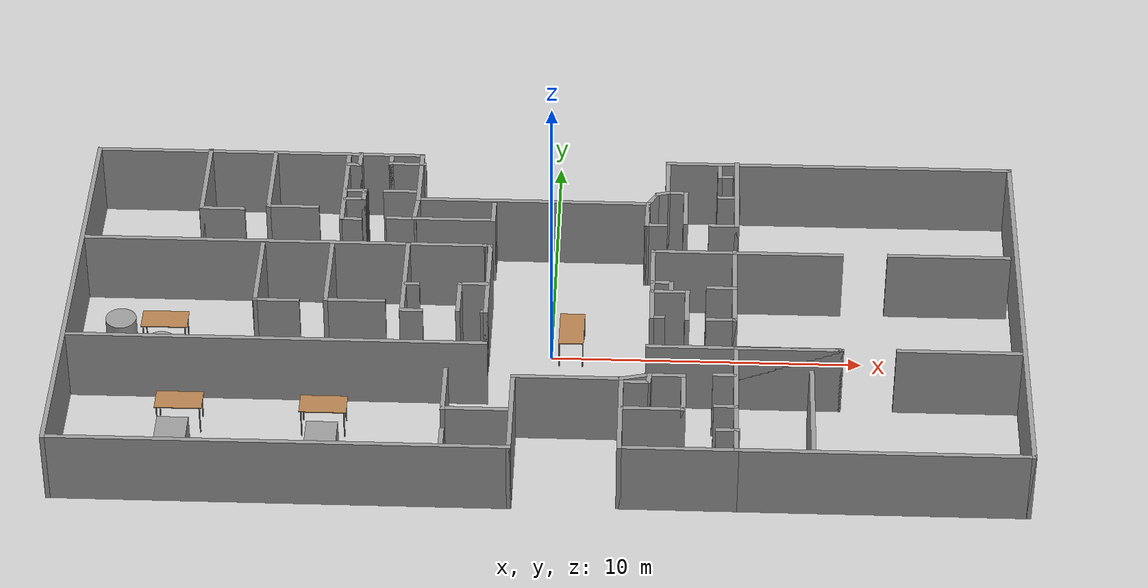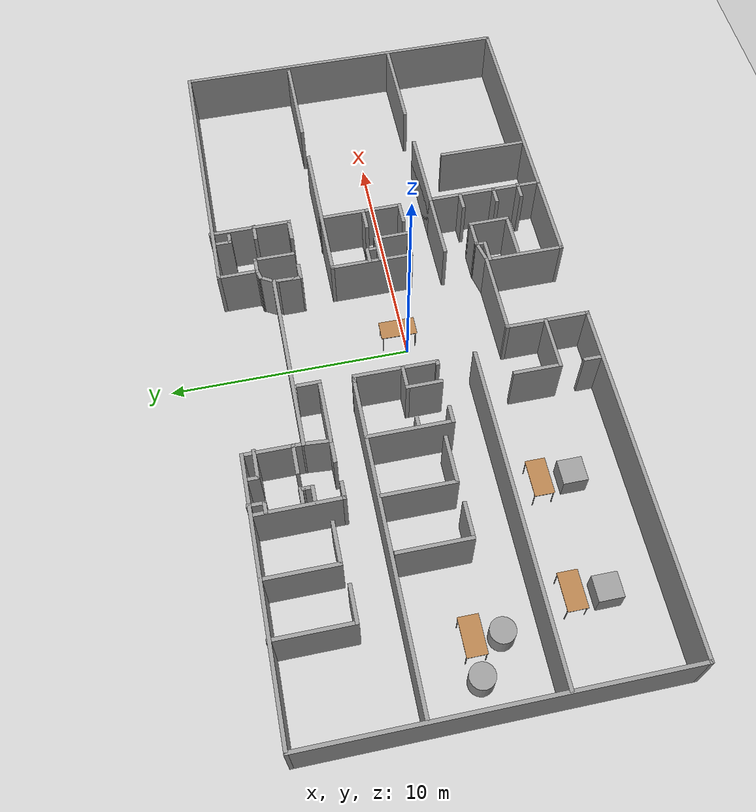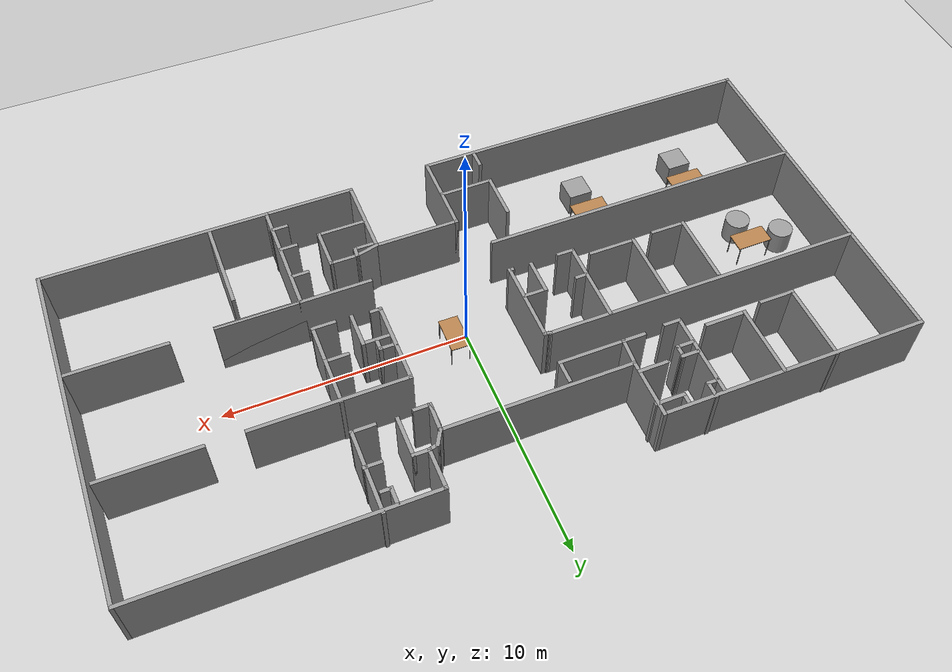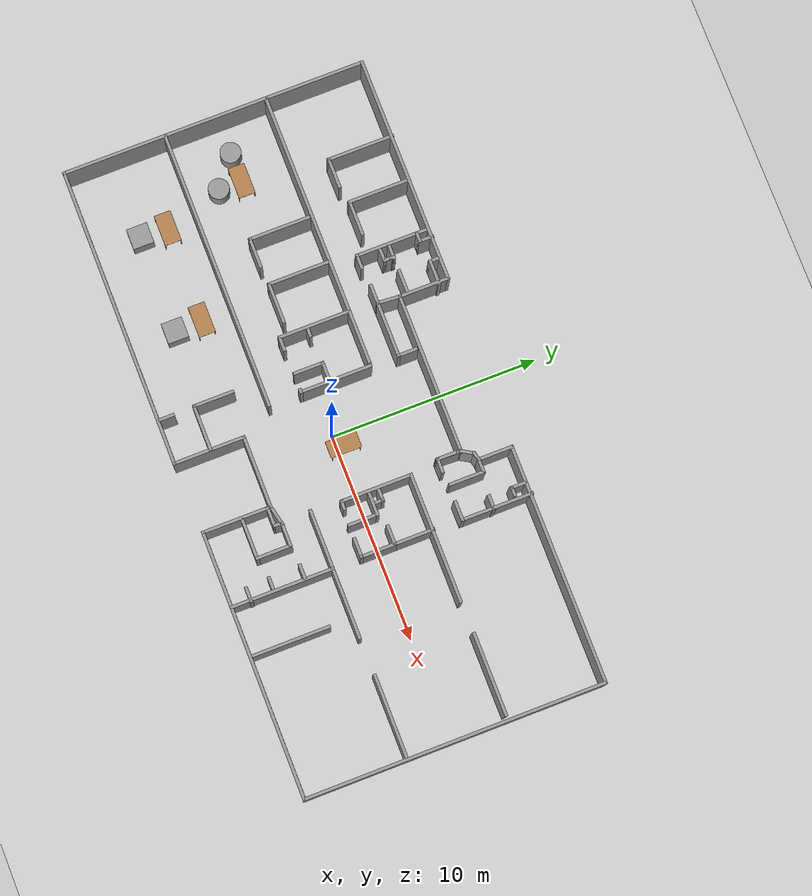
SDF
<sdf version="1.7">
 <world name="default">
  <light name="sun" type="directional">
   <pose>0 0 10 0 -0 0</pose>
   <diffuse>0.8 0.8 0.8 1</diffuse>
   <specular>0.2 0.2 0.2 1</specular>
   <attenuation>
    <range>1000</range>
    <constant>0.9</constant>
    <linear>0.01</linear>
    <quadratic>0.001</quadratic>
   </attenuation>
   <direction>-0.5 0.1 -0.9</direction>
   <spot><inner_angle>0</inner_angle><outer_angle>0</outer_angle><falloff>0</falloff></spot>
  </light>
  <model name="ground_plane">
   <static>1</static>
   <link name="link">
    <collision name="collision">
     <geometry><plane><normal>0 0 1</normal><size>100 100</size></plane></geometry>
     <surface>
      <contact><collide_bitmask>65535</collide_bitmask></contact>
      <friction><ode><mu>100</mu><mu2>50</mu2></ode></friction>
     </surface>
    </collision>
    <visual name="visual">
     <cast_shadows>0</cast_shadows>
     <geometry><plane><normal>0 0 1</normal><size>100 100</size></plane></geometry>
     <material>
      <script><uri>file://media/materials/scripts/gazebo.material</uri><name>Gazebo/Grey</name></script>
     </material>
    </visual>
   </link>
  </model>
  <gravity>0 0 -9.8</gravity>
  <magnetic_field>6e-06 2.3e-05 -4.2e-05</magnetic_field>
  <atmosphere type="adiabatic"/>
  <physics type="ode">
   <max_step_size>0.001</max_step_size>
   <real_time_factor>1</real_time_factor>
   <real_time_update_rate>1000</real_time_update_rate>
  </physics>
  <scene><ambient>0.4 0.4 0.4 1</ambient><background>0.7 0.7 0.7 1</background><shadows>1</shadows></scene>
  <spherical_coordinates>
   <surface_model>EARTH_WGS84</surface_model>
   <latitude_deg>0</latitude_deg>
   <longitude_deg>0</longitude_deg>
   <elevation>0</elevation>
   <heading_deg>0</heading_deg>
  </spherical_coordinates>
  <model name="HQ">
   <pose>-0.222632 0.129868 0 0 -0 0</pose>
   <link name="Wall_1">
    <collision name="Wall_1_Collision">
     <geometry><box><size>6.25 0.15 2.5</size></box></geometry>
     <pose>0 0 1.25 0 -0 0</pose>
    </collision>
    <visual name="Wall_1_Visual">
     <pose>0 0 1.25 0 -0 0</pose>
     <geometry><box><size>6.25 0.15 2.5</size></box></geometry>
     <material>
      <script><uri>file://media/materials/scripts/gazebo.material</uri><name>Gazebo/Grey</name></script>
      <ambient>1 1 1 1</ambient>
     </material>
     <meta><layer>0</layer></meta>
    </visual>
    <pose>6.38643 -2.35903 0 0 -0 0</pose>
   </link>
   <link name="Wall_10">
    <collision name="Wall_10_Collision">
     <geometry><box><size>2 0.15 2.5</size></box></geometry>
     <pose>0 0 1.25 0 -0 0</pose>
    </collision>
    <visual name="Wall_10_Visual">
     <pose>0 0 1.25 0 -0 0</pose>
     <geometry><box><size>2 0.15 2.5</size></box></geometry>
     <material>
      <script><uri>file://media/materials/scripts/gazebo.material</uri><name>Gazebo/Grey</name></script>
      <ambient>1 1 1 1</ambient>
     </material>
     <meta><layer>0</layer></meta>
    </visual>
    <pose>3.54404 -5.35903 0 0 -0 3.14159</pose>
   </link>
   <link name="Wall_100">
    <collision name="Wall_100_Collision">
     <geometry><box><size>13.25 0.15 2.5</size></box></geometry>
     <pose>0 0 1.25 0 -0 0</pose>
    </collision>
    <visual name="Wall_100_Visual">
     <pose>0 0 1.25 0 -0 0</pose>
     <geometry><box><size>13.25 0.15 2.5</size></box></geometry>
     <material>
      <script><uri>file://media/materials/scripts/gazebo.material</uri><name>Gazebo/Grey</name></script>
      <ambient>1 1 1 1</ambient>
     </material>
     <meta><layer>0</layer></meta>
    </visual>
    <pose>-8.61792 2.54532 0 0 -0 0</pose>
   </link>
   <link name="Wall_102">
    <collision name="Wall_102_Collision">
     <geometry><box><size>3.5 0.15 2.5</size></box></geometry>
     <pose>0 0 1.25 0 -0 0</pose>
    </collision>
    <visual name="Wall_102_Visual">
     <pose>0 0 1.25 0 -0 0</pose>
     <geometry><box><size>3.5 0.15 2.5</size></box></geometry>
     <material>
      <script><uri>file://media/materials/scripts/gazebo.material</uri><name>Gazebo/Grey</name></script>
      <ambient>1 1 1 1</ambient>
     </material>
     <meta><layer>0</layer></meta>
    </visual>
    <pose>-4.55922 0.835536 0 0 -0 -1.5708</pose>
   </link>
   <link name="Wall_103">
    <collision name="Wall_103_Collision">
     <geometry><box><size>0.75 0.15 2.5</size></box></geometry>
     <pose>0 0 1.25 0 -0 0</pose>
    </collision>
    <visual name="Wall_103_Visual">
     <pose>0 0 1.25 0 -0 0</pose>
     <geometry><box><size>0.75 0.15 2.5</size></box></geometry>
     <material>
      <script><uri>file://media/materials/scripts/gazebo.material</uri><name>Gazebo/Grey</name></script>
      <ambient>1 1 1 1</ambient>
     </material>
     <meta><layer>0</layer></meta>
    </visual>
    <pose>-4.25922 -0.839464 0 0 -0 0</pose>
   </link>
   <link name="Wall_105">
    <collision name="Wall_105_Collision">
     <geometry><box><size>0.25 0.15 2.5</size></box></geometry>
     <pose>0 0 1.25 0 -0 0</pose>
    </collision>
    <visual name="Wall_105_Visual">
     <pose>0 0 1.25 0 -0 0</pose>
     <geometry><box><size>0.25 0.15 2.5</size></box></geometry>
     <material>
      <script><uri>file://media/materials/scripts/gazebo.material</uri><name>Gazebo/Grey</name></script>
      <ambient>1 1 1 1</ambient>
     </material>
     <meta><layer>0</layer></meta>
    </visual>
    <pose>-2.01962 2.53238 0 0 -0 -0.261799</pose>
   </link>
   <link name="Wall_106">
    <collision name="Wall_106_Collision">
     <geometry><box><size>0.25 0.15 2.5</size></box></geometry>
     <pose>0 0 1.25 0 -0 0</pose>
    </collision>
    <visual name="Wall_106_Visual">
     <pose>0 0 1.25 0 -0 0</pose>
     <geometry><box><size>0.25 0.15 2.5</size></box></geometry>
     <material>
      <script><uri>file://media/materials/scripts/gazebo.material</uri><name>Gazebo/Grey</name></script>
      <ambient>1 1 1 1</ambient>
     </material>
     <meta><layer>0</layer></meta>
    </visual>
    <pose>-1.92133 2.51944 0 0 -0 0</pose>
   </link>
   <link name="Wall_107">
    <collision name="Wall_107_Collision">
     <geometry><box><size>3.5 0.15 2.5</size></box></geometry>
     <pose>0 0 1.25 0 -0 0</pose>
    </collision>
    <visual name="Wall_107_Visual">
     <pose>0 0 1.25 0 -0 0</pose>
     <geometry><box><size>3.5 0.15 2.5</size></box></geometry>
     <material>
      <script><uri>file://media/materials/scripts/gazebo.material</uri><name>Gazebo/Grey</name></script>
      <ambient>1 1 1 1</ambient>
     </material>
     <meta><layer>0</layer></meta>
    </visual>
    <pose>-1.87133 0.844437 0 0 -0 -1.5708</pose>
   </link>
   <link name="Wall_108">
    <collision name="Wall_108_Collision">
     <geometry><box><size>0.25 0.15 2.5</size></box></geometry>
     <pose>0 0 1.25 0 -0 0</pose>
    </collision>
    <visual name="Wall_108_Visual">
     <pose>0 0 1.25 0 -0 0</pose>
     <geometry><box><size>0.25 0.15 2.5</size></box></geometry>
     <material>
      <script><uri>file://media/materials/scripts/gazebo.material</uri><name>Gazebo/Grey</name></script>
      <ambient>1 1 1 1</ambient>
     </material>
     <meta><layer>0</layer></meta>
    </visual>
    <pose>-1.92133 -0.830563 0 0 -0 3.14159</pose>
   </link>
   <link name="Wall_110">
    <collision name="Wall_110_Collision">
     <geometry><box><size>1 0.15 2.5</size></box></geometry>
     <pose>0 0 1.25 0 -0 0</pose>
    </collision>
    <visual name="Wall_110_Visual">
     <pose>0 0 1.25 0 -0 0</pose>
     <geometry><box><size>1 0.15 2.5</size></box></geometry>
     <material>
      <script><uri>file://media/materials/scripts/gazebo.material</uri><name>Gazebo/Grey</name></script>
      <ambient>1 1 1 1</ambient>
     </material>
     <meta><layer>0</layer></meta>
    </visual>
    <pose>-2.34075 0.56271 0 0 -0 3.14159</pose>
   </link>
   <link name="Wall_111">
    <collision name="Wall_111_Collision">
     <geometry><box><size>1.5 0.15 2.5</size></box></geometry>
     <pose>0 0 1.25 0 -0 0</pose>
    </collision>
    <visual name="Wall_111_Visual">
     <pose>0 0 1.25 0 -0 0</pose>
     <geometry><box><size>1.5 0.15 2.5</size></box></geometry>
     <material>
      <script><uri>file://media/materials/scripts/gazebo.material</uri><name>Gazebo/Grey</name></script>
      <ambient>1 1 1 1</ambient>
     </material>
     <meta><layer>0</layer></meta>
    </visual>
    <pose>-2.76575 -0.11229 0 0 -0 -1.5708</pose>
   </link>
   <link name="Wall_113">
    <collision name="Wall_113_Collision">
     <geometry><box><size>0.5 0.15 2.5</size></box></geometry>
     <pose>0 0 1.25 0 -0 0</pose>
    </collision>
    <visual name="Wall_113_Visual">
     <pose>0 0 1.25 0 -0 0</pose>
     <geometry><box><size>0.5 0.15 2.5</size></box></geometry>
     <material>
      <script><uri>file://media/materials/scripts/gazebo.material</uri><name>Gazebo/Grey</name></script>
      <ambient>1 1 1 1</ambient>
     </material>
     <meta><layer>0</layer></meta>
    </visual>
    <pose>-4.31466 0.493145 0 0 -0 0</pose>
   </link>
   <link name="Wall_115">
    <collision name="Wall_115_Collision">
     <geometry><box><size>3 0.15 2.5</size></box></geometry>
     <pose>0 0 1.25 0 -0 0</pose>
    </collision>
    <visual name="Wall_115_Visual">
     <pose>0 0 1.25 0 -0 0</pose>
     <geometry><box><size>3 0.15 2.5</size></box></geometry>
     <material>
      <script><uri>file://media/materials/scripts/gazebo.material</uri><name>Gazebo/Grey</name></script>
      <ambient>1 1 1 1</ambient>
     </material>
     <meta><layer>0</layer></meta>
    </visual>
    <pose>-7.02879 1.01597 0 0 -0 -1.5708</pose>
   </link>
   <link name="Wall_116">
    <collision name="Wall_116_Collision">
     <geometry><box><size>2 0.15 2.5</size></box></geometry>
     <pose>0 0 1.25 0 -0 0</pose>
    </collision>
    <visual name="Wall_116_Visual">
     <pose>0 0 1.25 0 -0 0</pose>
     <geometry><box><size>2 0.15 2.5</size></box></geometry>
     <material>
      <script><uri>file://media/materials/scripts/gazebo.material</uri><name>Gazebo/Grey</name></script>
      <ambient>1 1 1 1</ambient>
     </material>
     <meta><layer>0</layer></meta>
    </visual>
    <pose>-6.10379 -0.409029 0 0 -0 0</pose>
   </link>
   <link name="Wall_118">
    <collision name="Wall_118_Collision">
     <geometry><box><size>3 0.15 2.5</size></box></geometry>
     <pose>0 0 1.25 0 -0 0</pose>
    </collision>
    <visual name="Wall_118_Visual">
     <pose>0 0 1.25 0 -0 0</pose>
     <geometry><box><size>3 0.15 2.5</size></box></geometry>
     <material>
      <script><uri>file://media/materials/scripts/gazebo.material</uri><name>Gazebo/Grey</name></script>
      <ambient>1 1 1 1</ambient>
     </material>
     <meta><layer>0</layer></meta>
    </visual>
    <pose>-9.28966 0.946406 0 0 -0 -1.5708</pose>
   </link>
   <link name="Wall_119">
    <collision name="Wall_119_Collision">
     <geometry><box><size>1.5 0.15 2.5</size></box></geometry>
     <pose>0 0 1.25 0 -0 0</pose>
    </collision>
    <visual name="Wall_119_Visual">
     <pose>0 0 1.25 0 -0 0</pose>
     <geometry><box><size>1.5 0.15 2.5</size></box></geometry>
     <material>
      <script><uri>file://media/materials/scripts/gazebo.material</uri><name>Gazebo/Grey</name></script>
      <ambient>1 1 1 1</ambient>
     </material>
     <meta><layer>0</layer></meta>
    </visual>
    <pose>-8.61466 -0.478594 0 0 -0 0</pose>
   </link>
   <link name="Wall_12">
    <collision name="Wall_12_Collision">
     <geometry><box><size>0.75 0.15 2.5</size></box></geometry>
     <pose>0 0 1.25 0 -0 0</pose>
    </collision>
    <visual name="Wall_12_Visual">
     <pose>0 0 1.25 0 -0 0</pose>
     <geometry><box><size>0.75 0.15 2.5</size></box></geometry>
     <material>
      <script><uri>file://media/materials/scripts/gazebo.material</uri><name>Gazebo/Grey</name></script>
      <ambient>1 1 1 1</ambient>
     </material>
     <meta><layer>0</layer></meta>
    </visual>
    <pose>5.75817 -3.68077 0 0 -0 0</pose>
   </link>
   <link name="Wall_121">
    <collision name="Wall_121_Collision">
     <geometry><box><size>13.5 0.15 2.5</size></box></geometry>
     <pose>0 0 1.25 0 -0 0</pose>
    </collision>
    <visual name="Wall_121_Visual">
     <pose>0 0 1.25 0 -0 0</pose>
     <geometry><box><size>13.5 0.15 2.5</size></box></geometry>
     <material>
      <script><uri>file://media/materials/scripts/gazebo.material</uri><name>Gazebo/Grey</name></script>
      <ambient>1 1 1 1</ambient>
     </material>
     <meta><layer>0</layer></meta>
    </visual>
    <pose>-8.49292 -2.39381 0 0 -0 0</pose>
   </link>
   <link name="Wall_123">
    <collision name="Wall_123_Collision">
     <geometry><box><size>2 0.15 2.5</size></box></geometry>
     <pose>0 0 1.25 0 -0 0</pose>
    </collision>
    <visual name="Wall_123_Visual">
     <pose>0 0 1.25 0 -0 0</pose>
     <geometry><box><size>2 0.15 2.5</size></box></geometry>
     <material>
      <script><uri>file://media/materials/scripts/gazebo.material</uri><name>Gazebo/Grey</name></script>
      <ambient>1 1 1 1</ambient>
     </material>
     <meta><layer>0</layer></meta>
    </visual>
    <pose>-2.99401 -4.64055 0 0 -0 -1.5708</pose>
   </link>
   <link name="Wall_125">
    <collision name="Wall_125_Collision">
     <geometry><box><size>0.75 0.15 2.5</size></box></geometry>
     <pose>0 0 1.25 0 -0 0</pose>
    </collision>
    <visual name="Wall_125_Visual">
     <pose>0 0 1.25 0 -0 0</pose>
     <geometry><box><size>0.75 0.15 2.5</size></box></geometry>
     <material>
      <script><uri>file://media/materials/scripts/gazebo.material</uri><name>Gazebo/Grey</name></script>
      <ambient>1 1 1 1</ambient>
     </material>
     <meta><layer>0</layer></meta>
    </visual>
    <pose>-2.95922 -6.90251 0 0 -0 -1.5708</pose>
   </link>
   <link name="Wall_127">
    <collision name="Wall_127_Collision">
     <geometry><box><size>2.25 0.15 2.5</size></box></geometry>
     <pose>0 0 1.25 0 -0 0</pose>
    </collision>
    <visual name="Wall_127_Visual">
     <pose>0 0 1.25 0 -0 0</pose>
     <geometry><box><size>2.25 0.15 2.5</size></box></geometry>
     <material>
      <script><uri>file://media/materials/scripts/gazebo.material</uri><name>Gazebo/Grey</name></script>
      <ambient>1 1 1 1</ambient>
     </material>
     <meta><layer>0</layer></meta>
    </visual>
    <pose>-1.94401 -5.56555 0 0 -0 0</pose>
   </link>
   <link name="Wall_129">
    <collision name="Wall_129_Collision">
     <geometry><box><size>1.06261 0.15 2.5</size></box></geometry>
     <pose>0 0 1.25 0 -0 0</pose>
    </collision>
    <visual name="Wall_129_Visual">
     <pose>0 0 1.25 0 -0 0</pose>
     <geometry><box><size>1.06261 0.15 2.5</size></box></geometry>
     <material>
      <script><uri>file://media/materials/scripts/gazebo.material</uri><name>Gazebo/Grey</name></script>
      <ambient>1 1 1 1</ambient>
     </material>
     <meta><layer>0</layer></meta>
    </visual>
    <pose>2.95978 -3.86413 0 0 -0 0.232417</pose>
   </link>
   <link name="Wall_14">
    <collision name="Wall_14_Collision">
     <geometry><box><size>0.75 0.15 2.5</size></box></geometry>
     <pose>0 0 1.25 0 -0 0</pose>
    </collision>
    <visual name="Wall_14_Visual">
     <pose>0 0 1.25 0 -0 0</pose>
     <geometry><box><size>0.75 0.15 2.5</size></box></geometry>
     <material>
      <script><uri>file://media/materials/scripts/gazebo.material</uri><name>Gazebo/Grey</name></script>
      <ambient>1 1 1 1</ambient>
     </material>
     <meta><layer>0</layer></meta>
    </visual>
    <pose>5.78425 -5.17642 0 0 -0 3.14159</pose>
   </link>
   <link name="Wall_16">
    <collision name="Wall_16_Collision">
     <geometry><box><size>0.75 0.15 2.5</size></box></geometry>
     <pose>0 0 1.25 0 -0 0</pose>
    </collision>
    <visual name="Wall_16_Visual">
     <pose>0 0 1.25 0 -0 0</pose>
     <geometry><box><size>0.75 0.15 2.5</size></box></geometry>
     <material>
      <script><uri>file://media/materials/scripts/gazebo.material</uri><name>Gazebo/Grey</name></script>
      <ambient>1 1 1 1</ambient>
     </material>
     <meta><layer>0</layer></meta>
    </visual>
    <pose>5.85382 -6.28946 0 0 -0 3.14159</pose>
   </link>
   <link name="Wall_18">
    <collision name="Wall_18_Collision">
     <geometry><box><size>9.25 0.15 2.5</size></box></geometry>
     <pose>0 0 1.25 0 -0 0</pose>
    </collision>
    <visual name="Wall_18_Visual">
     <pose>0 0 1.25 0 -0 0</pose>
     <geometry><box><size>9.25 0.15 2.5</size></box></geometry>
     <material>
      <script><uri>file://media/materials/scripts/gazebo.material</uri><name>Gazebo/Grey</name></script>
      <ambient>1 1 1 1</ambient>
     </material>
     <meta><layer>0</layer></meta>
    </visual>
    <pose>10.669 -7.20903 0 0 -0 0</pose>
   </link>
   <link name="Wall_19">
    <collision name="Wall_19_Collision">
     <geometry><box><size>14.5 0.15 2.5</size></box></geometry>
     <pose>0 0 1.25 0 -0 0</pose>
    </collision>
    <visual name="Wall_19_Visual">
     <pose>0 0 1.25 0 -0 0</pose>
     <geometry><box><size>14.5 0.15 2.5</size></box></geometry>
     <material>
      <script><uri>file://media/materials/scripts/gazebo.material</uri><name>Gazebo/Grey</name></script>
      <ambient>1 1 1 1</ambient>
     </material>
     <meta><layer>0</layer></meta>
    </visual>
    <pose>15.219 -0.034029 0 0 -0 1.5708</pose>
   </link>
   <link name="Wall_20">
    <collision name="Wall_20_Collision">
     <geometry><box><size>11.5 0.15 2.5</size></box></geometry>
     <pose>0 0 1.25 0 -0 0</pose>
    </collision>
    <visual name="Wall_20_Visual">
     <pose>0 0 1.25 0 -0 0</pose>
     <geometry><box><size>11.5 0.15 2.5</size></box></geometry>
     <material>
      <script><uri>file://media/materials/scripts/gazebo.material</uri><name>Gazebo/Grey</name></script>
      <ambient>1 1 1 1</ambient>
     </material>
     <meta><layer>0</layer></meta>
    </visual>
    <pose>9.54404 7.14097 0 0 -0 3.14159</pose>
   </link>
   <link name="Wall_21">
    <collision name="Wall_21_Collision">
     <geometry><box><size>1.75 0.15 2.5</size></box></geometry>
     <pose>0 0 1.25 0 -0 0</pose>
    </collision>
    <visual name="Wall_21_Visual">
     <pose>0 0 1.25 0 -0 0</pose>
     <geometry><box><size>1.75 0.15 2.5</size></box></geometry>
     <material>
      <script><uri>file://media/materials/scripts/gazebo.material</uri><name>Gazebo/Grey</name></script>
      <ambient>1 1 1 1</ambient>
     </material>
     <meta><layer>0</layer></meta>
    </visual>
    <pose>3.86904 6.34097 0 0 -0 -1.5708</pose>
   </link>
   <link name="Wall_22">
    <collision name="Wall_22_Collision">
     <geometry><box><size>0.5 0.15 2.5</size></box></geometry>
     <pose>0 0 1.25 0 -0 0</pose>
    </collision>
    <visual name="Wall_22_Visual">
     <pose>0 0 1.25 0 -0 0</pose>
     <geometry><box><size>0.5 0.15 2.5</size></box></geometry>
     <material>
      <script><uri>file://media/materials/scripts/gazebo.material</uri><name>Gazebo/Grey</name></script>
      <ambient>1 1 1 1</ambient>
     </material>
     <meta><layer>0</layer></meta>
    </visual>
    <pose>3.7 5.49568 0 0 -0 -2.87979</pose>
   </link>
   <link name="Wall_23">
    <collision name="Wall_23_Collision">
     <geometry><box><size>0.75 0.15 2.5</size></box></geometry>
     <pose>0 0 1.25 0 -0 0</pose>
    </collision>
    <visual name="Wall_23_Visual">
     <pose>0 0 1.25 0 -0 0</pose>
     <geometry><box><size>0.75 0.15 2.5</size></box></geometry>
     <material>
      <script><uri>file://media/materials/scripts/gazebo.material</uri><name>Gazebo/Grey</name></script>
      <ambient>1 1 1 1</ambient>
     </material>
     <meta><layer>0</layer></meta>
    </visual>
    <pose>3.38096 5.19058 0 0 -0 -2.0944</pose>
   </link>
   <link name="Wall_24">
    <collision name="Wall_24_Collision">
     <geometry><box><size>7.75 0.15 2.5</size></box></geometry>
     <pose>0 0 1.25 0 -0 0</pose>
    </collision>
    <visual name="Wall_24_Visual">
     <pose>0 0 1.25 0 -0 0</pose>
     <geometry><box><size>7.75 0.15 2.5</size></box></geometry>
     <material>
      <script><uri>file://media/materials/scripts/gazebo.material</uri><name>Gazebo/Grey</name></script>
      <ambient>1 1 1 1</ambient>
     </material>
     <meta><layer>0</layer></meta>
    </visual>
    <pose>-0.569037 4.93077 0 0 -0 3.14159</pose>
   </link>
   <link name="Wall_25">
    <collision name="Wall_25_Collision">
     <geometry><box><size>2.5 0.15 2.5</size></box></geometry>
     <pose>0 0 1.25 0 -0 0</pose>
    </collision>
    <visual name="Wall_25_Visual">
     <pose>0 0 1.25 0 -0 0</pose>
     <geometry><box><size>2.5 0.15 2.5</size></box></geometry>
     <material>
      <script><uri>file://media/materials/scripts/gazebo.material</uri><name>Gazebo/Grey</name></script>
      <ambient>1 1 1 1</ambient>
     </material>
     <meta><layer>0</layer></meta>
    </visual>
    <pose>-4.36904 6.10577 0 0 -0 1.5708</pose>
   </link>
   <link name="Wall_26">
    <collision name="Wall_26_Collision">
     <geometry><box><size>11 0.15 2.5</size></box></geometry>
     <pose>0 0 1.25 0 -0 0</pose>
    </collision>
    <visual name="Wall_26_Visual">
     <pose>0 0 1.25 0 -0 0</pose>
     <geometry><box><size>11 0.15 2.5</size></box></geometry>
     <material>
      <script><uri>file://media/materials/scripts/gazebo.material</uri><name>Gazebo/Grey</name></script>
      <ambient>1 1 1 1</ambient>
     </material>
     <meta><layer>0</layer></meta>
    </visual>
    <pose>-9.79404 7.28077 0 0 -0 3.14159</pose>
   </link>
   <link name="Wall_27">
    <collision name="Wall_27_Collision">
     <geometry><box><size>14.75 0.15 2.5</size></box></geometry>
     <pose>0 0 1.25 0 -0 0</pose>
    </collision>
    <visual name="Wall_27_Visual">
     <pose>0 0 1.25 0 -0 0</pose>
     <geometry><box><size>14.75 0.15 2.5</size></box></geometry>
     <material>
      <script><uri>file://media/materials/scripts/gazebo.material</uri><name>Gazebo/Grey</name></script>
      <ambient>1 1 1 1</ambient>
     </material>
     <meta><layer>0</layer></meta>
    </visual>
    <pose>-15.219 -0.019231 0 0 -0 -1.5708</pose>
   </link>
   <link name="Wall_28">
    <collision name="Wall_28_Collision">
     <geometry><box><size>14.5 0.15 2.5</size></box></geometry>
     <pose>0 0 1.25 0 -0 0</pose>
    </collision>
    <visual name="Wall_28_Visual">
     <pose>0 0 1.25 0 -0 0</pose>
     <geometry><box><size>14.5 0.15 2.5</size></box></geometry>
     <material>
      <script><uri>file://media/materials/scripts/gazebo.material</uri><name>Gazebo/Grey</name></script>
      <ambient>1 1 1 1</ambient>
     </material>
     <meta><layer>0</layer></meta>
    </visual>
    <pose>-8.04404 -7.31923 0 0 -0 0</pose>
   </link>
   <link name="Wall_29">
    <collision name="Wall_29_Collision">
     <geometry><box><size>3.5 0.15 2.5</size></box></geometry>
     <pose>0 0 1.25 0 -0 0</pose>
    </collision>
    <visual name="Wall_29_Visual">
     <pose>0 0 1.25 0 -0 0</pose>
     <geometry><box><size>3.5 0.15 2.5</size></box></geometry>
     <material>
      <script><uri>file://media/materials/scripts/gazebo.material</uri><name>Gazebo/Grey</name></script>
      <ambient>1 1 1 1</ambient>
     </material>
     <meta><layer>0</layer></meta>
    </visual>
    <pose>-0.869037 -5.64423 0 0 -0 1.5708</pose>
   </link>
   <link name="Wall_3">
    <collision name="Wall_3_Collision">
     <geometry><box><size>5 0.15 2.5</size></box></geometry>
     <pose>0 0 1.25 0 -0 0</pose>
    </collision>
    <visual name="Wall_3_Visual">
     <pose>0 0 1.25 0 -0 0</pose>
     <geometry><box><size>5 0.15 2.5</size></box></geometry>
     <material>
      <script><uri>file://media/materials/scripts/gazebo.material</uri><name>Gazebo/Grey</name></script>
      <ambient>1 1 1 1</ambient>
     </material>
     <meta><layer>0</layer></meta>
    </visual>
    <pose>6.11904 -4.78403 0 0 -0 -1.5708</pose>
   </link>
   <link name="Wall_30">
    <collision name="Wall_30_Collision">
     <geometry><box><size>3.5355 0.15 2.5</size></box></geometry>
     <pose>0 0 1.25 0 -0 0</pose>
    </collision>
    <visual name="Wall_30_Visual">
     <pose>0 0 1.25 0 -0 0</pose>
     <geometry><box><size>3.5355 0.15 2.5</size></box></geometry>
     <material>
      <script><uri>file://media/materials/scripts/gazebo.material</uri><name>Gazebo/Grey</name></script>
      <ambient>1 1 1 1</ambient>
     </material>
     <meta><layer>0</layer></meta>
    </visual>
    <pose>0.823354 -3.96923 0 0 -0 0</pose>
   </link>
   <link name="Wall_32">
    <collision name="Wall_32_Collision">
     <geometry><box><size>3.46739 0.15 2.5</size></box></geometry>
     <pose>0 0 1.25 0 -0 0</pose>
    </collision>
    <visual name="Wall_32_Visual">
     <pose>0 0 1.25 0 -0 0</pose>
     <geometry><box><size>3.46739 0.15 2.5</size></box></geometry>
     <material>
      <script><uri>file://media/materials/scripts/gazebo.material</uri><name>Gazebo/Grey</name></script>
      <ambient>1 1 1 1</ambient>
     </material>
     <meta><layer>0</layer></meta>
    </visual>
    <pose>7.77773 -2.35903 0 0 -0 0</pose>
   </link>
   <link name="Wall_34">
    <collision name="Wall_34_Collision">
     <geometry><box><size>3.75 0.15 2.5</size></box></geometry>
     <pose>0 0 1.25 0 -0 0</pose>
    </collision>
    <visual name="Wall_34_Visual">
     <pose>0 0 1.25 0 -0 0</pose>
     <geometry><box><size>3.75 0.15 2.5</size></box></geometry>
     <material>
      <script><uri>file://media/materials/scripts/gazebo.material</uri><name>Gazebo/Grey</name></script>
      <ambient>1 1 1 1</ambient>
     </material>
     <meta><layer>0</layer></meta>
    </visual>
    <pose>8.48425 -5.25468 0 0 -0 1.5708</pose>
   </link>
   <link name="Wall_36">
    <collision name="Wall_36_Collision">
     <geometry><box><size>4 0.15 2.5</size></box></geometry>
     <pose>0 0 1.25 0 -0 0</pose>
    </collision>
    <visual name="Wall_36_Visual">
     <pose>0 0 1.25 0 -0 0</pose>
     <geometry><box><size>4 0.15 2.5</size></box></geometry>
     <material>
      <script><uri>file://media/materials/scripts/gazebo.material</uri><name>Gazebo/Grey</name></script>
      <ambient>1 1 1 1</ambient>
     </material>
     <meta><layer>0</layer></meta>
    </visual>
    <pose>13.1679 -2.32425 0 0 -0 3.14159</pose>
   </link>
   <link name="Wall_38">
    <collision name="Wall_38_Collision">
     <geometry><box><size>4 0.15 2.5</size></box></geometry>
     <pose>0 0 1.25 0 -0 0</pose>
    </collision>
    <visual name="Wall_38_Visual">
     <pose>0 0 1.25 0 -0 0</pose>
     <geometry><box><size>4 0.15 2.5</size></box></geometry>
     <material>
      <script><uri>file://media/materials/scripts/gazebo.material</uri><name>Gazebo/Grey</name></script>
      <ambient>1 1 1 1</ambient>
     </material>
     <meta><layer>0</layer></meta>
    </visual>
    <pose>13.0288 2.47575 0 0 -0 3.14159</pose>
   </link>
   <link name="Wall_4">
    <collision name="Wall_4_Collision">
     <geometry><box><size>3.75 0.15 2.5</size></box></geometry>
     <pose>0 0 1.25 0 -0 0</pose>
    </collision>
    <visual name="Wall_4_Visual">
     <pose>0 0 1.25 0 -0 0</pose>
     <geometry><box><size>3.75 0.15 2.5</size></box></geometry>
     <material>
      <script><uri>file://media/materials/scripts/gazebo.material</uri><name>Gazebo/Grey</name></script>
      <ambient>1 1 1 1</ambient>
     </material>
     <meta><layer>0</layer></meta>
    </visual>
    <pose>4.31904 -7.20903 0 0 -0 3.14159</pose>
   </link>
   <link name="Wall_40">
    <collision name="Wall_40_Collision">
     <geometry><box><size>6.25 0.15 2.5</size></box></geometry>
     <pose>0 0 1.25 0 -0 0</pose>
    </collision>
    <visual name="Wall_40_Visual">
     <pose>0 0 1.25 0 -0 0</pose>
     <geometry><box><size>6.25 0.15 2.5</size></box></geometry>
     <material>
      <script><uri>file://media/materials/scripts/gazebo.material</uri><name>Gazebo/Grey</name></script>
      <ambient>1 1 1 1</ambient>
     </material>
     <meta><layer>0</layer></meta>
    </visual>
    <pose>6.47773 2.44097 0 0 -0 3.14159</pose>
   </link>
   <link name="Wall_41">
    <collision name="Wall_41_Collision">
     <geometry><box><size>3.5 0.15 2.5</size></box></geometry>
     <pose>0 0 1.25 0 -0 0</pose>
    </collision>
    <visual name="Wall_41_Visual">
     <pose>0 0 1.25 0 -0 0</pose>
     <geometry><box><size>3.5 0.15 2.5</size></box></geometry>
     <material>
      <script><uri>file://media/materials/scripts/gazebo.material</uri><name>Gazebo/Grey</name></script>
      <ambient>1 1 1 1</ambient>
     </material>
     <meta><layer>0</layer></meta>
    </visual>
    <pose>3.42773 0.765971 0 0 -0 -1.5708</pose>
   </link>
   <link name="Wall_42">
    <collision name="Wall_42_Collision">
     <geometry><box><size>0.5 0.15 2.5</size></box></geometry>
     <pose>0 0 1.25 0 -0 0</pose>
    </collision>
    <visual name="Wall_42_Visual">
     <pose>0 0 1.25 0 -0 0</pose>
     <geometry><box><size>0.5 0.15 2.5</size></box></geometry>
     <material>
      <script><uri>file://media/materials/scripts/gazebo.material</uri><name>Gazebo/Grey</name></script>
      <ambient>1 1 1 1</ambient>
     </material>
     <meta><layer>0</layer></meta>
    </visual>
    <pose>3.60273 -0.909029 0 0 -0 0</pose>
   </link>
   <link name="Wall_44">
    <collision name="Wall_44_Collision">
     <geometry><box><size>1.5 0.15 2.5</size></box></geometry>
     <pose>0 0 1.25 0 -0 0</pose>
    </collision>
    <visual name="Wall_44_Visual">
     <pose>0 0 1.25 0 -0 0</pose>
     <geometry><box><size>1.5 0.15 2.5</size></box></geometry>
     <material>
      <script><uri>file://media/materials/scripts/gazebo.material</uri><name>Gazebo/Grey</name></script>
      <ambient>1 1 1 1</ambient>
     </material>
     <meta><layer>0</layer></meta>
    </visual>
    <pose>4.55382 -0.292725 0 0 -0 1.5708</pose>
   </link>
   <link name="Wall_45">
    <collision name="Wall_45_Collision">
     <geometry><box><size>1.25 0.15 2.5</size></box></geometry>
     <pose>0 0 1.25 0 -0 0</pose>
    </collision>
    <visual name="Wall_45_Visual">
     <pose>0 0 1.25 0 -0 0</pose>
     <geometry><box><size>1.25 0.15 2.5</size></box></geometry>
     <material>
      <script><uri>file://media/materials/scripts/gazebo.material</uri><name>Gazebo/Grey</name></script>
      <ambient>1 1 1 1</ambient>
     </material>
     <meta><layer>0</layer></meta>
    </visual>
    <pose>4.00382 0.382275 0 0 -0 3.14159</pose>
   </link>
   <link name="Wall_47">
    <collision name="Wall_47_Collision">
     <geometry><box><size>0.5 0.15 2.5</size></box></geometry>
     <pose>0 0 1.25 0 -0 0</pose>
    </collision>
    <visual name="Wall_47_Visual">
     <pose>0 0 1.25 0 -0 0</pose>
     <geometry><box><size>0.5 0.15 2.5</size></box></geometry>
     <material>
      <script><uri>file://media/materials/scripts/gazebo.material</uri><name>Gazebo/Grey</name></script>
      <ambient>1 1 1 1</ambient>
     </material>
     <meta><layer>0</layer></meta>
    </visual>
    <pose>4.03208 0.668145 0 0 -0 1.5708</pose>
   </link>
   <link name="Wall_48">
    <collision name="Wall_48_Collision">
     <geometry><box><size>0.75 0.15 2.5</size></box></geometry>
     <pose>0 0 1.25 0 -0 0</pose>
    </collision>
    <visual name="Wall_48_Visual">
     <pose>0 0 1.25 0 -0 0</pose>
     <geometry><box><size>0.75 0.15 2.5</size></box></geometry>
     <material>
      <script><uri>file://media/materials/scripts/gazebo.material</uri><name>Gazebo/Grey</name></script>
      <ambient>1 1 1 1</ambient>
     </material>
     <meta><layer>0</layer></meta>
    </visual>
    <pose>3.73208 0.843145 0 0 -0 3.14159</pose>
   </link>
   <link name="Wall_5">
    <collision name="Wall_5_Collision">
     <geometry><box><size>3.25 0.15 2.5</size></box></geometry>
     <pose>0 0 1.25 0 -0 0</pose>
    </collision>
    <visual name="Wall_5_Visual">
     <pose>0 0 1.25 0 -0 0</pose>
     <geometry><box><size>3.25 0.15 2.5</size></box></geometry>
     <material>
      <script><uri>file://media/materials/scripts/gazebo.material</uri><name>Gazebo/Grey</name></script>
      <ambient>1 1 1 1</ambient>
     </material>
     <meta><layer>0</layer></meta>
    </visual>
    <pose>2.51904 -5.65903 0 0 -0 1.5708</pose>
   </link>
   <link name="Wall_50">
    <collision name="Wall_50_Collision">
     <geometry><box><size>2 0.15 2.5</size></box></geometry>
     <pose>0 0 1.25 0 -0 0</pose>
    </collision>
    <visual name="Wall_50_Visual">
     <pose>0 0 1.25 0 -0 0</pose>
     <geometry><box><size>2 0.15 2.5</size></box></geometry>
     <material>
      <script><uri>file://media/materials/scripts/gazebo.material</uri><name>Gazebo/Grey</name></script>
      <ambient>1 1 1 1</ambient>
     </material>
     <meta><layer>0</layer></meta>
    </visual>
    <pose>6.08425 1.55075 0 0 -0 -1.5708</pose>
   </link>
   <link name="Wall_51">
    <collision name="Wall_51_Collision">
     <geometry><box><size>1 0.15 2.5</size></box></geometry>
     <pose>0 0 1.25 0 -0 0</pose>
    </collision>
    <visual name="Wall_51_Visual">
     <pose>0 0 1.25 0 -0 0</pose>
     <geometry><box><size>1 0.15 2.5</size></box></geometry>
     <material>
      <script><uri>file://media/materials/scripts/gazebo.material</uri><name>Gazebo/Grey</name></script>
      <ambient>1 1 1 1</ambient>
     </material>
     <meta><layer>0</layer></meta>
    </visual>
    <pose>5.65925 0.625754 0 0 -0 3.14159</pose>
   </link>
   <link name="Wall_53">
    <collision name="Wall_53_Collision">
     <geometry><box><size>1.75 0.15 2.5</size></box></geometry>
     <pose>0 0 1.25 0 -0 0</pose>
    </collision>
    <visual name="Wall_53_Visual">
     <pose>0 0 1.25 0 -0 0</pose>
     <geometry><box><size>1.75 0.15 2.5</size></box></geometry>
     <material>
      <script><uri>file://media/materials/scripts/gazebo.material</uri><name>Gazebo/Grey</name></script>
      <ambient>1 1 1 1</ambient>
     </material>
     <meta><layer>0</layer></meta>
    </visual>
    <pose>6.08425 -0.174246 0 0 -0 -1.5708</pose>
   </link>
   <link name="Wall_54">
    <collision name="Wall_54_Collision">
     <geometry><box><size>1 0.15 2.5</size></box></geometry>
     <pose>0 0 1.25 0 -0 0</pose>
    </collision>
    <visual name="Wall_54_Visual">
     <pose>0 0 1.25 0 -0 0</pose>
     <geometry><box><size>1 0.15 2.5</size></box></geometry>
     <material>
      <script><uri>file://media/materials/scripts/gazebo.material</uri><name>Gazebo/Grey</name></script>
      <ambient>1 1 1 1</ambient>
     </material>
     <meta><layer>0</layer></meta>
    </visual>
    <pose>5.65925 -0.974246 0 0 -0 3.14159</pose>
   </link>
   <link name="Wall_56">
    <collision name="Wall_56_Collision">
     <geometry><box><size>3.5 0.15 2.5</size></box></geometry>
     <pose>0 0 1.25 0 -0 0</pose>
    </collision>
    <visual name="Wall_56_Visual">
     <pose>0 0 1.25 0 -0 0</pose>
     <geometry><box><size>3.5 0.15 2.5</size></box></geometry>
     <material>
      <script><uri>file://media/materials/scripts/gazebo.material</uri><name>Gazebo/Grey</name></script>
      <ambient>1 1 1 1</ambient>
     </material>
     <meta><layer>0</layer></meta>
    </visual>
    <pose>6.15382 5.53119 0 0 -0 -1.5708</pose>
   </link>
   <link name="Wall_57">
    <collision name="Wall_57_Collision">
     <geometry><box><size>1 0.15 2.5</size></box></geometry>
     <pose>0 0 1.25 0 -0 0</pose>
    </collision>
    <visual name="Wall_57_Visual">
     <pose>0 0 1.25 0 -0 0</pose>
     <geometry><box><size>1 0.15 2.5</size></box></geometry>
     <material>
      <script><uri>file://media/materials/scripts/gazebo.material</uri><name>Gazebo/Grey</name></script>
      <ambient>1 1 1 1</ambient>
     </material>
     <meta><layer>0</layer></meta>
    </visual>
    <pose>5.72882 3.85619 0 0 -0 3.14159</pose>
   </link>
   <link name="Wall_59">
    <collision name="Wall_59_Collision">
     <geometry><box><size>0.75 0.15 2.5</size></box></geometry>
     <pose>0 0 1.25 0 -0 0</pose>
    </collision>
    <visual name="Wall_59_Visual">
     <pose>0 0 1.25 0 -0 0</pose>
     <geometry><box><size>0.75 0.15 2.5</size></box></geometry>
     <material>
      <script><uri>file://media/materials/scripts/gazebo.material</uri><name>Gazebo/Grey</name></script>
      <ambient>1 1 1 1</ambient>
     </material>
     <meta><layer>0</layer></meta>
    </visual>
    <pose>5.5973 6.76054 0 0 -0 -1.5708</pose>
   </link>
   <link name="Wall_6">
    <collision name="Wall_6_Collision">
     <geometry><box><size>1 0.15 2.5</size></box></geometry>
     <pose>0 0 1.25 0 -0 0</pose>
    </collision>
    <visual name="Wall_6_Visual">
     <pose>0 0 1.25 0 -0 0</pose>
     <geometry><box><size>1 0.15 2.5</size></box></geometry>
     <material>
      <script><uri>file://media/materials/scripts/gazebo.material</uri><name>Gazebo/Grey</name></script>
      <ambient>1 1 1 1</ambient>
     </material>
     <meta><layer>0</layer></meta>
    </visual>
    <pose>2.94404 -4.10903 0 0 -0 0</pose>
   </link>
   <link name="Wall_60">
    <collision name="Wall_60_Collision">
     <geometry><box><size>0.5 0.15 2.5</size></box></geometry>
     <pose>0 0 1.25 0 -0 0</pose>
    </collision>
    <visual name="Wall_60_Visual">
     <pose>0 0 1.25 0 -0 0</pose>
     <geometry><box><size>0.5 0.15 2.5</size></box></geometry>
     <material>
      <script><uri>file://media/materials/scripts/gazebo.material</uri><name>Gazebo/Grey</name></script>
      <ambient>1 1 1 1</ambient>
     </material>
     <meta><layer>0</layer></meta>
    </visual>
    <pose>5.7723 6.46054 0 0 -0 0</pose>
   </link>
   <link name="Wall_62">
    <collision name="Wall_62_Collision">
     <geometry><box><size>1 0.15 2.5</size></box></geometry>
     <pose>0 0 1.25 0 -0 0</pose>
    </collision>
    <visual name="Wall_62_Visual">
     <pose>0 0 1.25 0 -0 0</pose>
     <geometry><box><size>1 0.15 2.5</size></box></geometry>
     <material>
      <script><uri>file://media/materials/scripts/gazebo.material</uri><name>Gazebo/Grey</name></script>
      <ambient>1 1 1 1</ambient>
     </material>
     <meta><layer>0</layer></meta>
    </visual>
    <pose>3.1973 4.24206 0 0 -0 -1.5708</pose>
   </link>
   <link name="Wall_63">
    <collision name="Wall_63_Collision">
     <geometry><box><size>0.75 0.15 2.5</size></box></geometry>
     <pose>0 0 1.25 0 -0 0</pose>
    </collision>
    <visual name="Wall_63_Visual">
     <pose>0 0 1.25 0 -0 0</pose>
     <geometry><box><size>0.75 0.15 2.5</size></box></geometry>
     <material>
      <script><uri>file://media/materials/scripts/gazebo.material</uri><name>Gazebo/Grey</name></script>
      <ambient>1 1 1 1</ambient>
     </material>
     <meta><layer>0</layer></meta>
    </visual>
    <pose>3.4973 3.81706 0 0 -0 0</pose>
   </link>
   <link name="Wall_65">
    <collision name="Wall_65_Collision">
     <geometry><box><size>0.75 0.15 2.5</size></box></geometry>
     <pose>0 0 1.25 0 -0 0</pose>
    </collision>
    <visual name="Wall_65_Visual">
     <pose>0 0 1.25 0 -0 0</pose>
     <geometry><box><size>0.75 0.15 2.5</size></box></geometry>
     <material>
      <script><uri>file://media/materials/scripts/gazebo.material</uri><name>Gazebo/Grey</name></script>
      <ambient>1 1 1 1</ambient>
     </material>
     <meta><layer>0</layer></meta>
    </visual>
    <pose>5.8886 5.36271 0 0 -0 3.14159</pose>
   </link>
   <link name="Wall_67">
    <collision name="Wall_67_Collision">
     <geometry><box><size>0.75 0.15 2.5</size></box></geometry>
     <pose>0 0 1.25 0 -0 0</pose>
    </collision>
    <visual name="Wall_67_Visual">
     <pose>0 0 1.25 0 -0 0</pose>
     <geometry><box><size>0.75 0.15 2.5</size></box></geometry>
     <material>
      <script><uri>file://media/materials/scripts/gazebo.material</uri><name>Gazebo/Grey</name></script>
      <ambient>1 1 1 1</ambient>
     </material>
     <meta><layer>0</layer></meta>
    </visual>
    <pose>4.16904 5.54097 0 0 -0 0</pose>
   </link>
   <link name="Wall_68">
    <collision name="Wall_68_Collision">
     <geometry><box><size>1.75 0.15 2.5</size></box></geometry>
     <pose>0 0 1.25 0 -0 0</pose>
    </collision>
    <visual name="Wall_68_Visual">
     <pose>0 0 1.25 0 -0 0</pose>
     <geometry><box><size>1.75 0.15 2.5</size></box></geometry>
     <material>
      <script><uri>file://media/materials/scripts/gazebo.material</uri><name>Gazebo/Grey</name></script>
      <ambient>1 1 1 1</ambient>
     </material>
     <meta><layer>0</layer></meta>
    </visual>
    <pose>4.46904 4.74097 0 0 -0 -1.5708</pose>
   </link>
   <link name="Wall_7">
    <collision name="Wall_7_Collision">
     <geometry><box><size>0.501724 0.15 2.5</size></box></geometry>
     <pose>0 0 1.25 0 -0 0</pose>
    </collision>
    <visual name="Wall_7_Visual">
     <pose>0 0 1.25 0 -0 0</pose>
     <geometry><box><size>0.501724 0.15 2.5</size></box></geometry>
     <material>
      <script><uri>file://media/materials/scripts/gazebo.material</uri><name>Gazebo/Grey</name></script>
      <ambient>1 1 1 1</ambient>
     </material>
     <meta><layer>0</layer></meta>
    </visual>
    <pose>3.38643 -3.93403 0 0 -0 1.47174</pose>
   </link>
   <link name="Wall_70">
    <collision name="Wall_70_Collision">
     <geometry><box><size>1.26422 0.15 2.5</size></box></geometry>
     <pose>0 0 1.25 0 -0 0</pose>
    </collision>
    <visual name="Wall_70_Visual">
     <pose>0 0 1.25 0 -0 0</pose>
     <geometry><box><size>1.26422 0.15 2.5</size></box></geometry>
     <material>
      <script><uri>file://media/materials/scripts/gazebo.material</uri><name>Gazebo/Grey</name></script>
      <ambient>1 1 1 1</ambient>
     </material>
     <meta><layer>0</layer></meta>
    </visual>
    <pose>3.21413 4.37391 0 0 -0 -1.60102</pose>
   </link>
   <link name="Wall_72">
    <collision name="Wall_72_Collision">
     <geometry><box><size>1 0.15 2.5</size></box></geometry>
     <pose>0 0 1.25 0 -0 0</pose>
    </collision>
    <visual name="Wall_72_Visual">
     <pose>0 0 1.25 0 -0 0</pose>
     <geometry><box><size>1 0.15 2.5</size></box></geometry>
     <material>
      <script><uri>file://media/materials/scripts/gazebo.material</uri><name>Gazebo/Grey</name></script>
      <ambient>1 1 1 1</ambient>
     </material>
     <meta><layer>0</layer></meta>
    </visual>
    <pose>-1.84618 4.31162 0 0 -0 -1.5708</pose>
   </link>
   <link name="Wall_73">
    <collision name="Wall_73_Collision">
     <geometry><box><size>2.75 0.15 2.5</size></box></geometry>
     <pose>0 0 1.25 0 -0 0</pose>
    </collision>
    <visual name="Wall_73_Visual">
     <pose>0 0 1.25 0 -0 0</pose>
     <geometry><box><size>2.75 0.15 2.5</size></box></geometry>
     <material>
      <script><uri>file://media/materials/scripts/gazebo.material</uri><name>Gazebo/Grey</name></script>
      <ambient>1 1 1 1</ambient>
     </material>
     <meta><layer>0</layer></meta>
    </visual>
    <pose>-3.14618 3.88662 0 0 -0 3.14159</pose>
   </link>
   <link name="Wall_74">
    <collision name="Wall_74_Collision">
     <geometry><box><size>1 0.15 2.5</size></box></geometry>
     <pose>0 0 1.25 0 -0 0</pose>
    </collision>
    <visual name="Wall_74_Visual">
     <pose>0 0 1.25 0 -0 0</pose>
     <geometry><box><size>1 0.15 2.5</size></box></geometry>
     <material>
      <script><uri>file://media/materials/scripts/gazebo.material</uri><name>Gazebo/Grey</name></script>
      <ambient>1 1 1 1</ambient>
     </material>
     <meta><layer>0</layer></meta>
    </visual>
    <pose>-4.87118 3.88662 0 0 -0 3.14159</pose>
   </link>
   <link name="Wall_76">
    <collision name="Wall_76_Collision">
     <geometry><box><size>1.19699 0.15 2.5</size></box></geometry>
     <pose>0 0 1.25 0 -0 0</pose>
    </collision>
    <visual name="Wall_76_Visual">
     <pose>0 0 1.25 0 -0 0</pose>
     <geometry><box><size>1.19699 0.15 2.5</size></box></geometry>
     <material>
      <script><uri>file://media/materials/scripts/gazebo.material</uri><name>Gazebo/Grey</name></script>
      <ambient>1 1 1 1</ambient>
     </material>
     <meta><layer>0</layer></meta>
    </visual>
    <pose>-4.40761 4.4087 0 0 -0 -1.64454</pose>
   </link>
   <link name="Wall_78">
    <collision name="Wall_78_Collision">
     <geometry><box><size>0.75 0.15 2.5</size></box></geometry>
     <pose>0 0 1.25 0 -0 0</pose>
    </collision>
    <visual name="Wall_78_Visual">
     <pose>0 0 1.25 0 -0 0</pose>
     <geometry><box><size>0.75 0.15 2.5</size></box></geometry>
     <material>
      <script><uri>file://media/materials/scripts/gazebo.material</uri><name>Gazebo/Grey</name></script>
      <ambient>1 1 1 1</ambient>
     </material>
     <meta><layer>0</layer></meta>
    </visual>
    <pose>-6.52879 3.79749 0 0 -0 3.14159</pose>
   </link>
   <link name="Wall_79">
    <collision name="Wall_79_Collision">
     <geometry><box><size>3.5 0.15 2.5</size></box></geometry>
     <pose>0 0 1.25 0 -0 0</pose>
    </collision>
    <visual name="Wall_79_Visual">
     <pose>0 0 1.25 0 -0 0</pose>
     <geometry><box><size>3.5 0.15 2.5</size></box></geometry>
     <material>
      <script><uri>file://media/materials/scripts/gazebo.material</uri><name>Gazebo/Grey</name></script>
      <ambient>1 1 1 1</ambient>
     </material>
     <meta><layer>0</layer></meta>
    </visual>
    <pose>-6.82879 5.47249 0 0 -0 1.5708</pose>
   </link>
   <link name="Wall_8">
    <collision name="Wall_8_Collision">
     <geometry><box><size>1.21522 0.15 2.5</size></box></geometry>
     <pose>0 0 1.25 0 -0 0</pose>
    </collision>
    <visual name="Wall_8_Visual">
     <pose>0 0 1.25 0 -0 0</pose>
     <geometry><box><size>1.21522 0.15 2.5</size></box></geometry>
     <material>
      <script><uri>file://media/materials/scripts/gazebo.material</uri><name>Gazebo/Grey</name></script>
      <ambient>1 1 1 1</ambient>
     </material>
     <meta><layer>0</layer></meta>
    </visual>
    <pose>3.93643 -3.75903 0 0 -0 0</pose>
   </link>
   <link name="Wall_81">
    <collision name="Wall_81_Collision">
     <geometry><box><size>0.5 0.15 2.5</size></box></geometry>
     <pose>0 0 1.25 0 -0 0</pose>
    </collision>
    <visual name="Wall_81_Visual">
     <pose>0 0 1.25 0 -0 0</pose>
     <geometry><box><size>0.5 0.15 2.5</size></box></geometry>
     <material>
      <script><uri>file://media/materials/scripts/gazebo.material</uri><name>Gazebo/Grey</name></script>
      <ambient>1 1 1 1</ambient>
     </material>
     <meta><layer>0</layer></meta>
    </visual>
    <pose>-6.61031 6.71923 0 0 -0 0</pose>
   </link>
   <link name="Wall_82">
    <collision name="Wall_82_Collision">
     <geometry><box><size>0.75 0.15 2.5</size></box></geometry>
     <pose>0 0 1.25 0 -0 0</pose>
    </collision>
    <visual name="Wall_82_Visual">
     <pose>0 0 1.25 0 -0 0</pose>
     <geometry><box><size>0.75 0.15 2.5</size></box></geometry>
     <material>
      <script><uri>file://media/materials/scripts/gazebo.material</uri><name>Gazebo/Grey</name></script>
      <ambient>1 1 1 1</ambient>
     </material>
     <meta><layer>0</layer></meta>
    </visual>
    <pose>-6.43531 7.01923 0 0 -0 1.5708</pose>
   </link>
   <link name="Wall_84">
    <collision name="Wall_84_Collision">
     <geometry><box><size>0.5 0.15 2.5</size></box></geometry>
     <pose>0 0 1.25 0 -0 0</pose>
    </collision>
    <visual name="Wall_84_Visual">
     <pose>0 0 1.25 0 -0 0</pose>
     <geometry><box><size>0.5 0.15 2.5</size></box></geometry>
     <material>
      <script><uri>file://media/materials/scripts/gazebo.material</uri><name>Gazebo/Grey</name></script>
      <ambient>1 1 1 1</ambient>
     </material>
     <meta><layer>0</layer></meta>
    </visual>
    <pose>-5.39401 6.98988 0 0 -0 -1.5708</pose>
   </link>
   <link name="Wall_85">
    <collision name="Wall_85_Collision">
     <geometry><box><size>1.25 0.15 2.5</size></box></geometry>
     <pose>0 0 1.25 0 -0 0</pose>
    </collision>
    <visual name="Wall_85_Visual">
     <pose>0 0 1.25 0 -0 0</pose>
     <geometry><box><size>1.25 0.15 2.5</size></box></geometry>
     <material>
      <script><uri>file://media/materials/scripts/gazebo.material</uri><name>Gazebo/Grey</name></script>
      <ambient>1 1 1 1</ambient>
     </material>
     <meta><layer>0</layer></meta>
    </visual>
    <pose>-4.84401 6.81488 0 0 -0 0</pose>
   </link>
   <link name="Wall_87">
    <collision name="Wall_87_Collision">
     <geometry><box><size>0.75 0.15 2.5</size></box></geometry>
     <pose>0 0 1.25 0 -0 0</pose>
    </collision>
    <visual name="Wall_87_Visual">
     <pose>0 0 1.25 0 -0 0</pose>
     <geometry><box><size>0.75 0.15 2.5</size></box></geometry>
     <material>
      <script><uri>file://media/materials/scripts/gazebo.material</uri><name>Gazebo/Grey</name></script>
      <ambient>1 1 1 1</ambient>
     </material>
     <meta><layer>0</layer></meta>
    </visual>
    <pose>-6.45053 5.32793 0 0 -0 0</pose>
   </link>
   <link name="Wall_88">
    <collision name="Wall_88_Collision">
     <geometry><box><size>0.25 0.15 2.5</size></box></geometry>
     <pose>0 0 1.25 0 -0 0</pose>
    </collision>
    <visual name="Wall_88_Visual">
     <pose>0 0 1.25 0 -0 0</pose>
     <geometry><box><size>0.25 0.15 2.5</size></box></geometry>
     <material>
      <script><uri>file://media/materials/scripts/gazebo.material</uri><name>Gazebo/Grey</name></script>
      <ambient>1 1 1 1</ambient>
     </material>
     <meta><layer>0</layer></meta>
    </visual>
    <pose>-6.16347 5.27963 0 0 -0 -1.8326</pose>
   </link>
   <link name="Wall_89">
    <collision name="Wall_89_Collision">
     <geometry><box><size>0.5 0.15 2.5</size></box></geometry>
     <pose>0 0 1.25 0 -0 0</pose>
    </collision>
    <visual name="Wall_89_Visual">
     <pose>0 0 1.25 0 -0 0</pose>
     <geometry><box><size>0.5 0.15 2.5</size></box></geometry>
     <material>
      <script><uri>file://media/materials/scripts/gazebo.material</uri><name>Gazebo/Grey</name></script>
      <ambient>1 1 1 1</ambient>
     </material>
     <meta><layer>0</layer></meta>
    </visual>
    <pose>-6.17641 5.05633 0 0 -0 -1.5708</pose>
   </link>
   <link name="Wall_9">
    <collision name="Wall_9_Collision">
     <geometry><box><size>1.75 0.15 2.5</size></box></geometry>
     <pose>0 0 1.25 0 -0 0</pose>
    </collision>
    <visual name="Wall_9_Visual">
     <pose>0 0 1.25 0 -0 0</pose>
     <geometry><box><size>1.75 0.15 2.5</size></box></geometry>
     <material>
      <script><uri>file://media/materials/scripts/gazebo.material</uri><name>Gazebo/Grey</name></script>
      <ambient>1 1 1 1</ambient>
     </material>
     <meta><layer>0</layer></meta>
    </visual>
    <pose>4.46904 -4.55903 0 0 -0 -1.5708</pose>
   </link>
   <link name="Wall_90">
    <collision name="Wall_90_Collision">
     <geometry><box><size>0.75 0.15 2.5</size></box></geometry>
     <pose>0 0 1.25 0 -0 0</pose>
    </collision>
    <visual name="Wall_90_Visual">
     <pose>0 0 1.25 0 -0 0</pose>
     <geometry><box><size>0.75 0.15 2.5</size></box></geometry>
     <material>
      <script><uri>file://media/materials/scripts/gazebo.material</uri><name>Gazebo/Grey</name></script>
      <ambient>1 1 1 1</ambient>
     </material>
     <meta><layer>0</layer></meta>
    </visual>
    <pose>-6.47641 4.88133 0 0 -0 3.14159</pose>
   </link>
   <link name="Wall_92">
    <collision name="Wall_92_Collision">
     <geometry><box><size>1.25 0.15 2.5</size></box></geometry>
     <pose>0 0 1.25 0 -0 0</pose>
    </collision>
    <visual name="Wall_92_Visual">
     <pose>0 0 1.25 0 -0 0</pose>
     <geometry><box><size>1.25 0.15 2.5</size></box></geometry>
     <material>
      <script><uri>file://media/materials/scripts/gazebo.material</uri><name>Gazebo/Grey</name></script>
      <ambient>1 1 1 1</ambient>
     </material>
     <meta><layer>0</layer></meta>
    </visual>
    <pose>-4.92879 5.32793 0 0 -0 3.14159</pose>
   </link>
   <link name="Wall_94">
    <collision name="Wall_94_Collision">
     <geometry><box><size>3 0.15 2.5</size></box></geometry>
     <pose>0 0 1.25 0 -0 0</pose>
    </collision>
    <visual name="Wall_94_Visual">
     <pose>0 0 1.25 0 -0 0</pose>
     <geometry><box><size>3 0.15 2.5</size></box></geometry>
     <material>
      <script><uri>file://media/materials/scripts/gazebo.material</uri><name>Gazebo/Grey</name></script>
      <ambient>1 1 1 1</ambient>
     </material>
     <meta><layer>0</layer></meta>
    </visual>
    <pose>-9.28966 5.81597 0 0 -0 -1.5708</pose>
   </link>
   <link name="Wall_95">
    <collision name="Wall_95_Collision">
     <geometry><box><size>1.75 0.15 2.5</size></box></geometry>
     <pose>0 0 1.25 0 -0 0</pose>
    </collision>
    <visual name="Wall_95_Visual">
     <pose>0 0 1.25 0 -0 0</pose>
     <geometry><box><size>1.75 0.15 2.5</size></box></geometry>
     <material>
      <script><uri>file://media/materials/scripts/gazebo.material</uri><name>Gazebo/Grey</name></script>
      <ambient>1 1 1 1</ambient>
     </material>
     <meta><layer>0</layer></meta>
    </visual>
    <pose>-8.48966 4.39097 0 0 -0 0</pose>
   </link>
   <link name="Wall_97">
    <collision name="Wall_97_Collision">
     <geometry><box><size>3.25 0.15 2.5</size></box></geometry>
     <pose>0 0 1.25 0 -0 0</pose>
    </collision>
    <visual name="Wall_97_Visual">
     <pose>0 0 1.25 0 -0 0</pose>
     <geometry><box><size>3.25 0.15 2.5</size></box></geometry>
     <material>
      <script><uri>file://media/materials/scripts/gazebo.material</uri><name>Gazebo/Grey</name></script>
      <ambient>1 1 1 1</ambient>
     </material>
     <meta><layer>0</layer></meta>
    </visual>
    <pose>-11.481 5.76054 0 0 -0 -1.5708</pose>
   </link>
   <link name="Wall_98">
    <collision name="Wall_98_Collision">
     <geometry><box><size>1.5 0.15 2.5</size></box></geometry>
     <pose>0 0 1.25 0 -0 0</pose>
    </collision>
    <visual name="Wall_98_Visual">
     <pose>0 0 1.25 0 -0 0</pose>
     <geometry><box><size>1.5 0.15 2.5</size></box></geometry>
     <material>
      <script><uri>file://media/materials/scripts/gazebo.material</uri><name>Gazebo/Grey</name></script>
      <ambient>1 1 1 1</ambient>
     </material>
     <meta><layer>0</layer></meta>
    </visual>
    <pose>-10.806 4.21054 0 0 -0 0</pose>
   </link>
   <static>1</static>
  </model>
  <model name="table">
   <static>1</static>
   <link name="link">
    <collision name="surface">
     <pose>0 0 1 0 -0 0</pose>
     <geometry><box><size>1.5 0.8 0.03</size></box></geometry>
     <surface><friction><ode><mu>0.6</mu><mu2>0.6</mu2></ode></friction></surface>
    </collision>
    <visual name="visual1">
     <pose>0 0 1 0 -0 0</pose>
     <geometry><box><size>1.5 0.8 0.03</size></box></geometry>
     <material>
      <script><uri>file://media/materials/scripts/gazebo.material</uri><name>Gazebo/Wood</name></script>
     </material>
    </visual>
    <collision name="front_left_leg">
     <pose>0.68 0.38 0.5 0 -0 0</pose>
     <geometry><cylinder><radius>0.02</radius><length>1</length></cylinder></geometry>
    </collision>
    <visual name="front_left_leg">
     <pose>0.68 0.38 0.5 0 -0 0</pose>
     <geometry><cylinder><radius>0.02</radius><length>1</length></cylinder></geometry>
     <material>
      <script><uri>file://media/materials/scripts/gazebo.material</uri><name>Gazebo/Grey</name></script>
     </material>
    </visual>
    <collision name="front_right_leg">
     <pose>0.68 -0.38 0.5 0 -0 0</pose>
     <geometry><cylinder><radius>0.02</radius><length>1</length></cylinder></geometry>
    </collision>
    <visual name="front_right_leg">
     <pose>0.68 -0.38 0.5 0 -0 0</pose>
     <geometry><cylinder><radius>0.02</radius><length>1</length></cylinder></geometry>
     <material>
      <script><uri>file://media/materials/scripts/gazebo.material</uri><name>Gazebo/Grey</name></script>
     </material>
    </visual>
    <collision name="back_right_leg">
     <pose>-0.68 -0.38 0.5 0 -0 0</pose>
     <geometry><cylinder><radius>0.02</radius><length>1</length></cylinder></geometry>
    </collision>
    <visual name="back_right_leg">
     <pose>-0.68 -0.38 0.5 0 -0 0</pose>
     <geometry><cylinder><radius>0.02</radius><length>1</length></cylinder></geometry>
     <material>
      <script><uri>file://media/materials/scripts/gazebo.material</uri><name>Gazebo/Grey</name></script>
     </material>
    </visual>
    <collision name="back_left_leg">
     <pose>-0.68 0.38 0.5 0 -0 0</pose>
     <geometry><cylinder><radius>0.02</radius><length>1</length></cylinder></geometry>
    </collision>
    <visual name="back_left_leg">
     <pose>-0.68 0.38 0.5 0 -0 0</pose>
     <geometry><cylinder><radius>0.02</radius><length>1</length></cylinder></geometry>
     <material>
      <script><uri>file://media/materials/scripts/gazebo.material</uri><name>Gazebo/Grey</name></script>
     </material>
    </visual>
   </link>
   <pose>-11.6852 -3.63136 0 0 -0 0</pose>
  </model>
  <model name="table_0">
   <static>1</static>
   <link name="link">
    <collision name="surface">
     <pose>0 0 1 0 -0 0</pose>
     <geometry><box><size>1.5 0.8 0.03</size></box></geometry>
     <surface><friction><ode><mu>0.6</mu><mu2>0.6</mu2></ode></friction></surface>
    </collision>
    <visual name="visual1">
     <pose>0 0 1 0 -0 0</pose>
     <geometry><box><size>1.5 0.8 0.03</size></box></geometry>
     <material>
      <script><uri>file://media/materials/scripts/gazebo.material</uri><name>Gazebo/Wood</name></script>
     </material>
    </visual>
    <collision name="front_left_leg">
     <pose>0.68 0.38 0.5 0 -0 0</pose>
     <geometry><cylinder><radius>0.02</radius><length>1</length></cylinder></geometry>
    </collision>
    <visual name="front_left_leg">
     <pose>0.68 0.38 0.5 0 -0 0</pose>
     <geometry><cylinder><radius>0.02</radius><length>1</length></cylinder></geometry>
     <material>
      <script><uri>file://media/materials/scripts/gazebo.material</uri><name>Gazebo/Grey</name></script>
     </material>
    </visual>
    <collision name="front_right_leg">
     <pose>0.68 -0.38 0.5 0 -0 0</pose>
     <geometry><cylinder><radius>0.02</radius><length>1</length></cylinder></geometry>
    </collision>
    <visual name="front_right_leg">
     <pose>0.68 -0.38 0.5 0 -0 0</pose>
     <geometry><cylinder><radius>0.02</radius><length>1</length></cylinder></geometry>
     <material>
      <script><uri>file://media/materials/scripts/gazebo.material</uri><name>Gazebo/Grey</name></script>
     </material>
    </visual>
    <collision name="back_right_leg">
     <pose>-0.68 -0.38 0.5 0 -0 0</pose>
     <geometry><cylinder><radius>0.02</radius><length>1</length></cylinder></geometry>
    </collision>
    <visual name="back_right_leg">
     <pose>-0.68 -0.38 0.5 0 -0 0</pose>
     <geometry><cylinder><radius>0.02</radius><length>1</length></cylinder></geometry>
     <material>
      <script><uri>file://media/materials/scripts/gazebo.material</uri><name>Gazebo/Grey</name></script>
     </material>
    </visual>
    <collision name="back_left_leg">
     <pose>-0.68 0.38 0.5 0 -0 0</pose>
     <geometry><cylinder><radius>0.02</radius><length>1</length></cylinder></geometry>
    </collision>
    <visual name="back_left_leg">
     <pose>-0.68 0.38 0.5 0 -0 0</pose>
     <geometry><cylinder><radius>0.02</radius><length>1</length></cylinder></geometry>
     <material>
      <script><uri>file://media/materials/scripts/gazebo.material</uri><name>Gazebo/Grey</name></script>
     </material>
    </visual>
   </link>
   <pose>-7.10475 -3.67905 0 0 -0 0</pose>
  </model>
  <model name="table_1">
   <static>1</static>
   <link name="link">
    <collision name="surface">
     <pose>0 0 1 0 -0 0</pose>
     <geometry><box><size>1.5 0.8 0.03</size></box></geometry>
     <surface><friction><ode><mu>0.6</mu><mu2>0.6</mu2></ode></friction></surface>
    </collision>
    <visual name="visual1">
     <pose>0 0 1 0 -0 0</pose>
     <geometry><box><size>1.5 0.8 0.03</size></box></geometry>
     <material>
      <script><uri>file://media/materials/scripts/gazebo.material</uri><name>Gazebo/Wood</name></script>
     </material>
    </visual>
    <collision name="front_left_leg">
     <pose>0.68 0.38 0.5 0 -0 0</pose>
     <geometry><cylinder><radius>0.02</radius><length>1</length></cylinder></geometry>
    </collision>
    <visual name="front_left_leg">
     <pose>0.68 0.38 0.5 0 -0 0</pose>
     <geometry><cylinder><radius>0.02</radius><length>1</length></cylinder></geometry>
     <material>
      <script><uri>file://media/materials/scripts/gazebo.material</uri><name>Gazebo/Grey</name></script>
     </material>
    </visual>
    <collision name="front_right_leg">
     <pose>0.68 -0.38 0.5 0 -0 0</pose>
     <geometry><cylinder><radius>0.02</radius><length>1</length></cylinder></geometry>
    </collision>
    <visual name="front_right_leg">
     <pose>0.68 -0.38 0.5 0 -0 0</pose>
     <geometry><cylinder><radius>0.02</radius><length>1</length></cylinder></geometry>
     <material>
      <script><uri>file://media/materials/scripts/gazebo.material</uri><name>Gazebo/Grey</name></script>
     </material>
    </visual>
    <collision name="back_right_leg">
     <pose>-0.68 -0.38 0.5 0 -0 0</pose>
     <geometry><cylinder><radius>0.02</radius><length>1</length></cylinder></geometry>
    </collision>
    <visual name="back_right_leg">
     <pose>-0.68 -0.38 0.5 0 -0 0</pose>
     <geometry><cylinder><radius>0.02</radius><length>1</length></cylinder></geometry>
     <material>
      <script><uri>file://media/materials/scripts/gazebo.material</uri><name>Gazebo/Grey</name></script>
     </material>
    </visual>
    <collision name="back_left_leg">
     <pose>-0.68 0.38 0.5 0 -0 0</pose>
     <geometry><cylinder><radius>0.02</radius><length>1</length></cylinder></geometry>
    </collision>
    <visual name="back_left_leg">
     <pose>-0.68 0.38 0.5 0 -0 0</pose>
     <geometry><cylinder><radius>0.02</radius><length>1</length></cylinder></geometry>
     <material>
      <script><uri>file://media/materials/scripts/gazebo.material</uri><name>Gazebo/Grey</name></script>
     </material>
    </visual>
   </link>
   <pose>-12.5601 0.343493 0 0 -0 0</pose>
  </model>
  <model name="table_2">
   <static>1</static>
   <link name="link">
    <collision name="surface">
     <pose>0 0 1 0 -0 0</pose>
     <geometry><box><size>1.5 0.8 0.03</size></box></geometry>
     <surface><friction><ode><mu>0.6</mu><mu2>0.6</mu2></ode></friction></surface>
    </collision>
    <visual name="visual1">
     <pose>0 0 1 0 -0 0</pose>
     <geometry><box><size>1.5 0.8 0.03</size></box></geometry>
     <material>
      <script><uri>file://media/materials/scripts/gazebo.material</uri><name>Gazebo/Wood</name></script>
     </material>
    </visual>
    <collision name="front_left_leg">
     <pose>0.68 0.38 0.5 0 -0 0</pose>
     <geometry><cylinder><radius>0.02</radius><length>1</length></cylinder></geometry>
    </collision>
    <visual name="front_left_leg">
     <pose>0.68 0.38 0.5 0 -0 0</pose>
     <geometry><cylinder><radius>0.02</radius><length>1</length></cylinder></geometry>
     <material>
      <script><uri>file://media/materials/scripts/gazebo.material</uri><name>Gazebo/Grey</name></script>
     </material>
    </visual>
    <collision name="front_right_leg">
     <pose>0.68 -0.38 0.5 0 -0 0</pose>
     <geometry><cylinder><radius>0.02</radius><length>1</length></cylinder></geometry>
    </collision>
    <visual name="front_right_leg">
     <pose>0.68 -0.38 0.5 0 -0 0</pose>
     <geometry><cylinder><radius>0.02</radius><length>1</length></cylinder></geometry>
     <material>
      <script><uri>file://media/materials/scripts/gazebo.material</uri><name>Gazebo/Grey</name></script>
     </material>
    </visual>
    <collision name="back_right_leg">
     <pose>-0.68 -0.38 0.5 0 -0 0</pose>
     <geometry><cylinder><radius>0.02</radius><length>1</length></cylinder></geometry>
    </collision>
    <visual name="back_right_leg">
     <pose>-0.68 -0.38 0.5 0 -0 0</pose>
     <geometry><cylinder><radius>0.02</radius><length>1</length></cylinder></geometry>
     <material>
      <script><uri>file://media/materials/scripts/gazebo.material</uri><name>Gazebo/Grey</name></script>
     </material>
    </visual>
    <collision name="back_left_leg">
     <pose>-0.68 0.38 0.5 0 -0 0</pose>
     <geometry><cylinder><radius>0.02</radius><length>1</length></cylinder></geometry>
    </collision>
    <visual name="back_left_leg">
     <pose>-0.68 0.38 0.5 0 -0 0</pose>
     <geometry><cylinder><radius>0.02</radius><length>1</length></cylinder></geometry>
     <material>
      <script><uri>file://media/materials/scripts/gazebo.material</uri><name>Gazebo/Grey</name></script>
     </material>
    </visual>
   </link>
   <pose>0.635633 0.313805 0 0 0 -1.57969</pose>
  </model>
  <model name="unit_box">
   <pose>-11.7987 -4.94473 0.499995 -1e-05 -0 -0</pose>
   <link name="link">
    <inertial>
     <mass>1</mass>
     <inertia>
      <ixx>0.166667</ixx>
      <ixy>0</ixy>
      <ixz>0</ixz>
      <iyy>0.166667</iyy>
      <iyz>0</iyz>
      <izz>0.166667</izz>
     </inertia>
    </inertial>
    <collision name="collision"><geometry><box><size>1 1 1</size></box></geometry></collision>
    <visual name="visual">
     <geometry><box><size>1 1 1</size></box></geometry>
     <material>
      <script><name>Gazebo/Grey</name><uri>file://media/materials/scripts/gazebo.material</uri></script>
     </material>
    </visual>
   </link>
  </model>
  <model name="unit_box_0">
   <pose>-7.07918 -5.00069 0.499995 0 1e-05 0</pose>
   <link name="link">
    <inertial>
     <mass>1</mass>
     <inertia>
      <ixx>0.166667</ixx>
      <ixy>0</ixy>
      <ixz>0</ixz>
      <iyy>0.166667</iyy>
      <iyz>0</iyz>
      <izz>0.166667</izz>
     </inertia>
    </inertial>
    <collision name="collision"><geometry><box><size>1 1 1</size></box></geometry></collision>
    <visual name="visual">
     <geometry><box><size>1 1 1</size></box></geometry>
     <material>
      <script><name>Gazebo/Grey</name><uri>file://media/materials/scripts/gazebo.material</uri></script>
     </material>
    </visual>
   </link>
  </model>
  <model name="unit_cylinder">
   <pose>-12.5841 -0.773449 0.499993 -3e-06 -4e-06 -0</pose>
   <link name="link">
    <inertial>
     <mass>1</mass>
     <inertia><ixx>0.145833</ixx><ixy>0</ixy><ixz>0</ixz><iyy>0.145833</iyy><iyz>0</iyz><izz>0.125</izz></inertia>
    </inertial>
    <collision name="collision">
     <geometry><cylinder><radius>0.5</radius><length>1</length></cylinder></geometry>
    </collision>
    <visual name="visual">
     <geometry><cylinder><radius>0.5</radius><length>1</length></cylinder></geometry>
     <material>
      <script><name>Gazebo/Grey</name><uri>file://media/materials/scripts/gazebo.material</uri></script>
     </material>
    </visual>
   </link>
  </model>
  <model name="unit_cylinder_0">
   <pose>-13.9981 0.337332 0.499997 3e-06 4e-06 -0</pose>
   <link name="link">
    <inertial>
     <mass>1</mass>
     <inertia><ixx>0.145833</ixx><ixy>0</ixy><ixz>0</ixz><iyy>0.145833</iyy><iyz>0</iyz><izz>0.125</izz></inertia>
    </inertial>
    <collision name="collision">
     <geometry><cylinder><radius>0.5</radius><length>1</length></cylinder></geometry>
    </collision>
    <visual name="visual">
     <geometry><cylinder><radius>0.5</radius><length>1</length></cylinder></geometry>
     <material>
      <script><name>Gazebo/Grey</name><uri>file://media/materials/scripts/gazebo.material</uri></script>
     </material>
    </visual>
   </link>
  </model>
  <sensor name="force_torque" type="force_torque"><update_rate>30</update_rate></sensor>
 </world>
</sdf>
